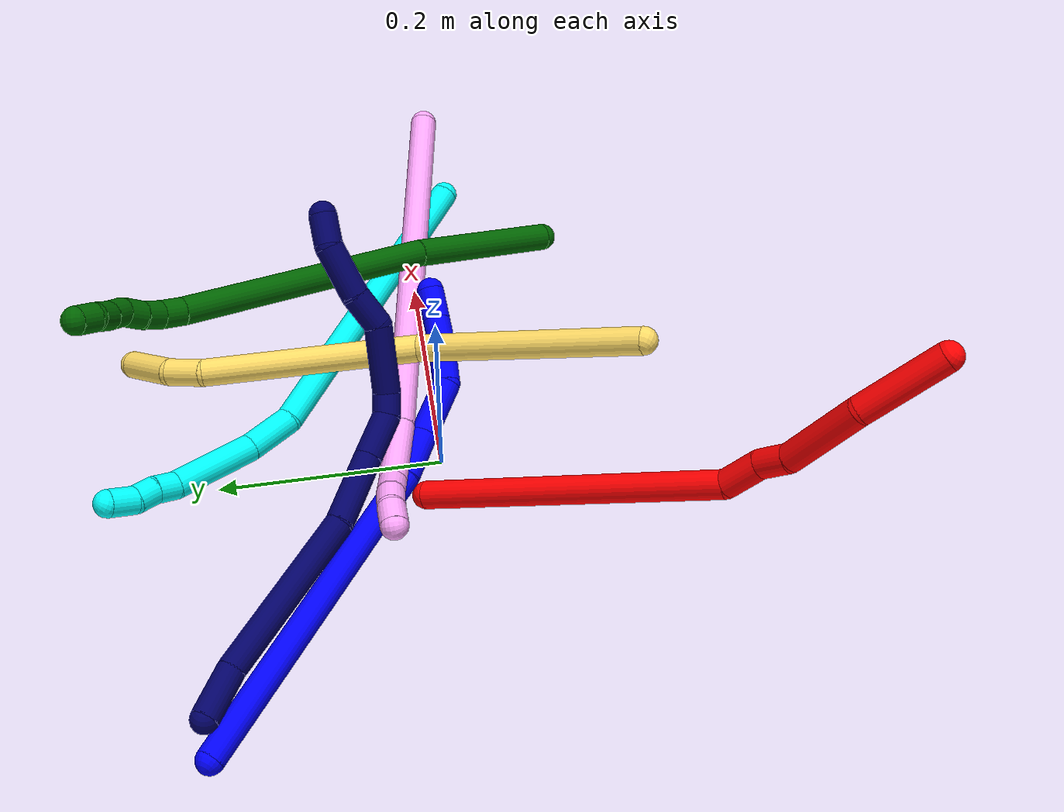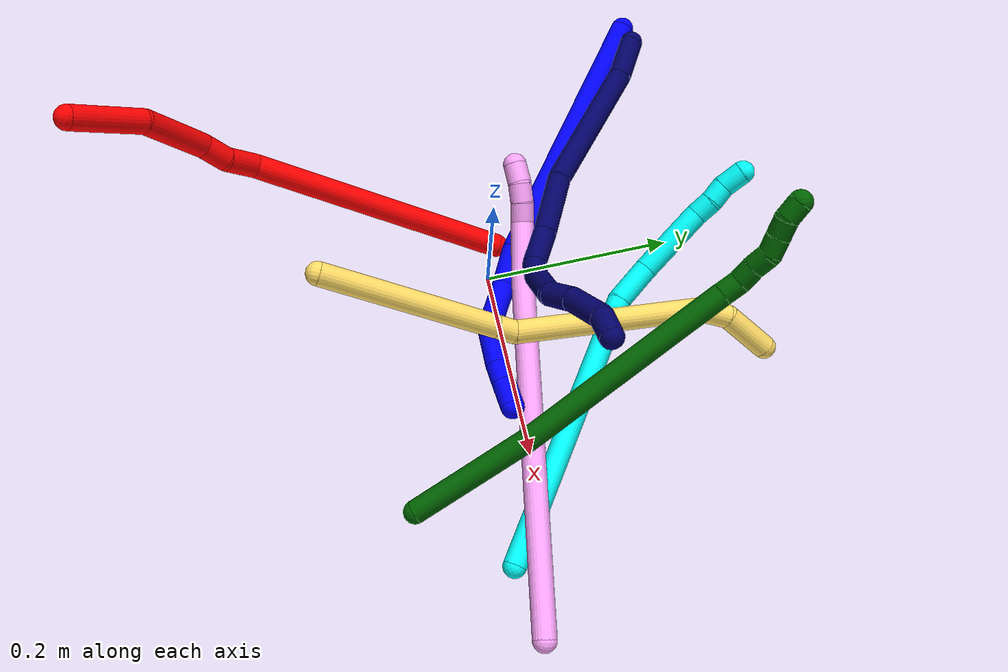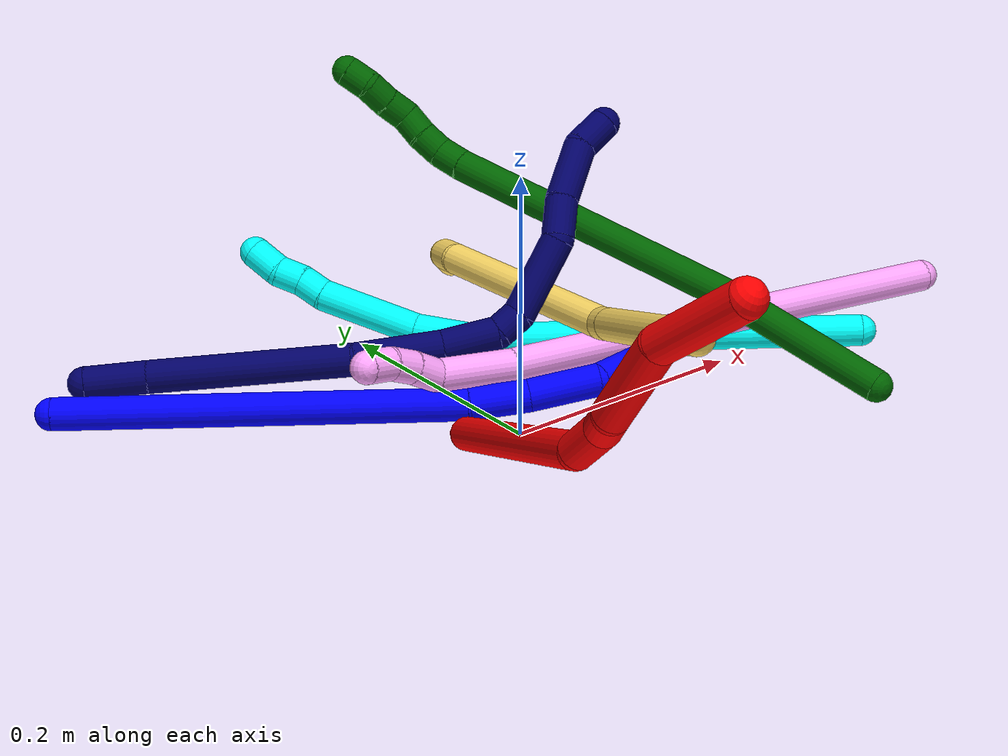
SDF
<sdf version="1.7">
 <world name="default">
  <plugin name="TubeGeneratorPlugin" filename="libtube_generator_plugin.so"/>
  <model name="photoneo_s_sensor">
   <static>1</static>
   <pose>0 0 2 1.57079 1.57079 3.14159</pose>
   <link name="link">
    <inertial><mass>0.1</mass></inertial>
    <sensor name="sensor" type="depth">
     <update_rate>30</update_rate>
     <camera>
      <horizontal_fov>1.22</horizontal_fov>
      <image><width>1920</width><height>1200</height><format>B8G8R8</format></image>
      <clip><near>0.1</near><far>4</far></clip>
      <depth_camera><output>points</output></depth_camera>
     </camera>
     <plugin name="camera_plugin" filename="libgazebo_ros_depth_camera.so">
      <baseline>0.2</baseline>
      <alwaysOn>1</alwaysOn>
      <updateRate>0.0</updateRate>
      <cameraName>camera_ir</cameraName>
      <imageTopicName>/camera/color/image_raw</imageTopicName>
      <cameraInfoTopicName>/camera/color/camera_info</cameraInfoTopicName>
      <depthImageTopicName>/camera/depth/image_raw</depthImageTopicName>
      <depthImageCameraInfoTopicName>/camera/depth/camera_info</depthImageCameraInfoTopicName>
      <pointCloudTopicName>/camera/depth/points</pointCloudTopicName>
      <frameName>fr_optical</frameName>
      <pointCloudCutoff>0.1</pointCloudCutoff>
      <pointCloudCutoffMax>2.0</pointCloudCutoffMax>
      <distortionK1>0</distortionK1>
      <distortionK2>0</distortionK2>
      <distortionK3>0</distortionK3>
      <distortionT1>0</distortionT1>
      <distortionT2>0</distortionT2>
      <CxPrime>0</CxPrime>
      <Cx>0</Cx>
      <Cy>0</Cy>
      <focalLength>0</focalLength>
      <hackBaseline>0</hackBaseline>
     </plugin>
    </sensor>
   </link>
  </model>
  <gravity>0 0 -9.8</gravity>
  <magnetic_field>6e-06 2.3e-05 -4.2e-05</magnetic_field>
  <atmosphere type="adiabatic"/>
  <physics name="default_physics" default="0" type="ode">
   <max_step_size>0.003</max_step_size>
   <real_time_factor>1</real_time_factor>
   <real_time_update_rate>1000</real_time_update_rate>
   <max_contacts>10000</max_contacts>
   <ode>
    <solver>
     <type>quick</type>
     <iters>100</iters>
     <sor>1.3</sor>
     <use_dynamic_moi_rescaling>0</use_dynamic_moi_rescaling>
    </solver>
    <constraints>
     <contact_max_correcting_vel>0</contact_max_correcting_vel>
     <contact_surface_layer>0.001</contact_surface_layer>
     <cfm>0</cfm>
     <erp>0.2</erp>
    </constraints>
   </ode>
  </physics>
  <scene><ambient>0.4 0.4 0.4 1</ambient><background>0.7 0.7 0.7 1</background><shadows>0</shadows></scene>
  <audio><device>default</device></audio>
  <spherical_coordinates>
   <surface_model>EARTH_WGS84</surface_model>
   <latitude_deg>0</latitude_deg>
   <longitude_deg>0</longitude_deg>
   <elevation>0</elevation>
   <heading_deg>0</heading_deg>
  </spherical_coordinates>
  <model name="bin">
   <static>1</static>
   <link name="bottom">
    <collision name="collision-bottom">
     <pose>0 0 -0.01 0 -0 0</pose>
     <geometry><box><size>0.8 0.6 0.02</size></box></geometry>
     <surface>
      <friction><ode><mu>100</mu><mu2>100</mu2></ode></friction>
      <contact><collide_bitmask>65535</collide_bitmask></contact>
     </surface>
    </collision>
   </link>
   <link name="west_wall">
    <collision name="collision-west_wall">
     <pose>-0.41 0 0.1 0 -0 0</pose>
     <geometry><box><size>0.02 0.6 0.2</size></box></geometry>
     <surface>
      <friction><ode><mu>100</mu><mu2>100</mu2></ode></friction>
      <contact><collide_bitmask>65535</collide_bitmask></contact>
     </surface>
    </collision>
   </link>
   <link name="east_wall">
    <collision name="collision-east_wall">
     <pose>0.41 0 0.1 0 -0 0</pose>
     <geometry><box><size>0.02 0.6 0.2</size></box></geometry>
     <surface>
      <friction><ode><mu>100</mu><mu2>100</mu2></ode></friction>
      <contact><collide_bitmask>65535</collide_bitmask></contact>
     </surface>
    </collision>
   </link>
   <link name="south_wall">
    <collision name="collision-south_wall">
     <pose>0 -0.31 0.1 0 -0 0</pose>
     <geometry><box><size>0.8 0.02 0.2</size></box></geometry>
     <surface>
      <friction><ode><mu>100</mu><mu2>100</mu2></ode></friction>
      <contact><collide_bitmask>65535</collide_bitmask></contact>
     </surface>
    </collision>
   </link>
   <link name="north_wall">
    <collision name="collision-north_wall">
     <pose>0 0.31 0.1 0 -0 0</pose>
     <geometry><box><size>0.8 0.02 0.2</size></box></geometry>
     <surface>
      <friction><ode><mu>100</mu><mu2>100</mu2></ode></friction>
      <contact><collide_bitmask>65535</collide_bitmask></contact>
     </surface>
    </collision>
   </link>
  </model>
  <model name="1">
   <static>0</static>
   <link name="1">
    <collision name="collision-cylinder-e_1_1_4">
     <pose>-0.007108 -0.011797 -0.151948 3.06411 -0.046606 -1.08274</pose>
     <geometry><cylinder><radius>0.0125</radius><length>0.305142</length></cylinder></geometry>
     <surface>
      <friction><ode><mu>1.16</mu><mu2>1.16</mu2><slip1>0</slip1><slip2>0</slip2></ode></friction>
      <contact><ode><kp>1e+06</kp><kd>1</kd><max_vel>0</max_vel><min_depth>0.001</min_depth></ode></contact>
     </surface>
    </collision>
    <visual name="visual-cylinder-e_1_1_4">
     <pose>-0.007108 -0.011797 -0.151948 3.06411 -0.046606 -1.08274</pose>
     <geometry><cylinder><radius>0.0125</radius><length>0.305142</length></cylinder></geometry>
     <material><ambient>0 0 1 1</ambient></material>
    </visual>
    <collision name="collision-cylinder-e_2_4_5">
     <pose>-0.011288 -0.024881 -0.326158 3.08386 0.130588 2.30991</pose>
     <geometry><cylinder><radius>0.0125</radius><length>0.044981</length></cylinder></geometry>
     <surface>
      <friction><ode><mu>1.16</mu><mu2>1.16</mu2><slip1>0</slip1><slip2>0</slip2></ode></friction>
      <contact><ode><kp>1e+06</kp><kd>1</kd><max_vel>0</max_vel><min_depth>0.001</min_depth></ode></contact>
     </surface>
    </collision>
    <visual name="visual-cylinder-e_2_4_5">
     <pose>-0.011288 -0.024881 -0.326158 3.08386 0.130588 2.30991</pose>
     <geometry><cylinder><radius>0.0125</radius><length>0.044981</length></cylinder></geometry>
     <material><ambient>0 0 1 1</ambient></material>
    </visual>
    <collision name="collision-cylinder-e_3_5_6">
     <pose>-0.004905 -0.030956 -0.374732 2.9616 0.12845 1.23838</pose>
     <geometry><cylinder><radius>0.0125</radius><length>0.053933</length></cylinder></geometry>
     <surface>
      <friction><ode><mu>1.16</mu><mu2>1.16</mu2><slip1>0</slip1><slip2>0</slip2></ode></friction>
      <contact><ode><kp>1e+06</kp><kd>1</kd><max_vel>0</max_vel><min_depth>0.001</min_depth></ode></contact>
     </surface>
    </collision>
    <visual name="visual-cylinder-e_3_5_6">
     <pose>-0.004905 -0.030956 -0.374732 2.9616 0.12845 1.23838</pose>
     <geometry><cylinder><radius>0.0125</radius><length>0.053933</length></cylinder></geometry>
     <material><ambient>0 0 1 1</ambient></material>
    </visual>
    <collision name="collision-cylinder-e_4_6_7">
     <pose>0.010289 -0.034239 -0.41915 -3.05865 0.573642 -2.86207</pose>
     <geometry><cylinder><radius>0.0125</radius><length>0.043262</length></cylinder></geometry>
     <surface>
      <friction><ode><mu>1.16</mu><mu2>1.16</mu2><slip1>0</slip1><slip2>0</slip2></ode></friction>
      <contact><ode><kp>1e+06</kp><kd>1</kd><max_vel>0</max_vel><min_depth>0.001</min_depth></ode></contact>
     </surface>
    </collision>
    <visual name="visual-cylinder-e_4_6_7">
     <pose>0.010289 -0.034239 -0.41915 -3.05865 0.573642 -2.86207</pose>
     <geometry><cylinder><radius>0.0125</radius><length>0.043262</length></cylinder></geometry>
     <material><ambient>0 0 1 1</ambient></material>
    </visual>
    <collision name="collision-cylinder-e_5_7_8">
     <pose>0.029648 -0.033719 -0.445978 3.02912 0.714929 2.8424</pose>
     <geometry><cylinder><radius>0.0125</radius><length>0.023247</length></cylinder></geometry>
     <surface>
      <friction><ode><mu>1.16</mu><mu2>1.16</mu2><slip1>0</slip1><slip2>0</slip2></ode></friction>
      <contact><ode><kp>1e+06</kp><kd>1</kd><max_vel>0</max_vel><min_depth>0.001</min_depth></ode></contact>
     </surface>
    </collision>
    <visual name="visual-cylinder-e_5_7_8">
     <pose>0.029648 -0.033719 -0.445978 3.02912 0.714929 2.8424</pose>
     <geometry><cylinder><radius>0.0125</radius><length>0.023247</length></cylinder></geometry>
     <material><ambient>0 0 1 1</ambient></material>
    </visual>
    <collision name="collision-cylinder-e_6_8_2">
     <pose>0.046965 -0.035866 -0.46571 3.0364 0.719322 2.8634</pose>
     <geometry><cylinder><radius>0.0125</radius><length>0.029435</length></cylinder></geometry>
     <surface>
      <friction><ode><mu>1.16</mu><mu2>1.16</mu2><slip1>0</slip1><slip2>0</slip2></ode></friction>
      <contact><ode><kp>1e+06</kp><kd>1</kd><max_vel>0</max_vel><min_depth>0.001</min_depth></ode></contact>
     </surface>
    </collision>
    <visual name="visual-cylinder-e_6_8_2">
     <pose>0.046965 -0.035866 -0.46571 3.0364 0.719322 2.8634</pose>
     <geometry><cylinder><radius>0.0125</radius><length>0.029435</length></cylinder></geometry>
     <material><ambient>0 0 1 1</ambient></material>
    </visual>
    <collision name="collision-sphere-2">
     <pose>0.056662 -0.037029 -0.47672 0 -0 0</pose>
     <geometry><sphere><radius>0.0125</radius></sphere></geometry>
     <surface>
      <friction><ode><mu>1.16</mu><mu2>1.16</mu2><slip1>0</slip1><slip2>0</slip2></ode></friction>
      <contact><ode><kp>1e+06</kp><kd>1</kd><max_vel>0</max_vel><min_depth>0.001</min_depth></ode></contact>
     </surface>
    </collision>
    <visual name="visual-sphere-2">
     <pose>0.056662 -0.037029 -0.47672 0 -0 0</pose>
     <geometry><sphere><radius>0.0125</radius></sphere></geometry>
     <material><ambient>0 0 1 1</ambient></material>
    </visual>
    <collision name="collision-sphere-4">
     <pose>-0.014216 -0.023595 -0.303896 0 -0 0</pose>
     <geometry><sphere><radius>0.0125</radius></sphere></geometry>
     <surface>
      <friction><ode><mu>1.16</mu><mu2>1.16</mu2><slip1>0</slip1><slip2>0</slip2></ode></friction>
      <contact><ode><kp>1e+06</kp><kd>1</kd><max_vel>0</max_vel><min_depth>0.001</min_depth></ode></contact>
     </surface>
    </collision>
    <visual name="visual-sphere-4">
     <pose>-0.014216 -0.023595 -0.303896 0 -0 0</pose>
     <geometry><sphere><radius>0.0125</radius></sphere></geometry>
     <material><ambient>0 0 1 1</ambient></material>
    </visual>
    <collision name="collision-sphere-1">
     <geometry><sphere><radius>0.0125</radius></sphere></geometry>
     <surface>
      <friction><ode><mu>1.16</mu><mu2>1.16</mu2><slip1>0</slip1><slip2>0</slip2></ode></friction>
      <contact><ode><kp>1e+06</kp><kd>1</kd><max_vel>0</max_vel><min_depth>0.001</min_depth></ode></contact>
     </surface>
    </collision>
    <visual name="visual-sphere-1">
     <geometry><sphere><radius>0.0125</radius></sphere></geometry>
     <material><ambient>0 0 1 1</ambient></material>
    </visual>
    <collision name="collision-sphere-8">
     <pose>0.037268 -0.034704 -0.4547 0 -0 0</pose>
     <geometry><sphere><radius>0.0125</radius></sphere></geometry>
     <surface>
      <friction><ode><mu>1.16</mu><mu2>1.16</mu2><slip1>0</slip1><slip2>0</slip2></ode></friction>
      <contact><ode><kp>1e+06</kp><kd>1</kd><max_vel>0</max_vel><min_depth>0.001</min_depth></ode></contact>
     </surface>
    </collision>
    <visual name="visual-sphere-8">
     <pose>0.037268 -0.034704 -0.4547 0 -0 0</pose>
     <geometry><sphere><radius>0.0125</radius></sphere></geometry>
     <material><ambient>0 0 1 1</ambient></material>
    </visual>
    <collision name="collision-sphere-5">
     <pose>-0.008359 -0.026168 -0.34842 0 -0 0</pose>
     <geometry><sphere><radius>0.0125</radius></sphere></geometry>
     <surface>
      <friction><ode><mu>1.16</mu><mu2>1.16</mu2><slip1>0</slip1><slip2>0</slip2></ode></friction>
      <contact><ode><kp>1e+06</kp><kd>1</kd><max_vel>0</max_vel><min_depth>0.001</min_depth></ode></contact>
     </surface>
    </collision>
    <visual name="visual-sphere-5">
     <pose>-0.008359 -0.026168 -0.34842 0 -0 0</pose>
     <geometry><sphere><radius>0.0125</radius></sphere></geometry>
     <material><ambient>0 0 1 1</ambient></material>
    </visual>
    <collision name="collision-sphere-6">
     <pose>-0.00145 -0.035744 -0.401044 0 -0 0</pose>
     <geometry><sphere><radius>0.0125</radius></sphere></geometry>
     <surface>
      <friction><ode><mu>1.16</mu><mu2>1.16</mu2><slip1>0</slip1><slip2>0</slip2></ode></friction>
      <contact><ode><kp>1e+06</kp><kd>1</kd><max_vel>0</max_vel><min_depth>0.001</min_depth></ode></contact>
     </surface>
    </collision>
    <visual name="visual-sphere-6">
     <pose>-0.00145 -0.035744 -0.401044 0 -0 0</pose>
     <geometry><sphere><radius>0.0125</radius></sphere></geometry>
     <material><ambient>0 0 1 1</ambient></material>
    </visual>
    <collision name="collision-sphere-7">
     <pose>0.022028 -0.032733 -0.437256 0 -0 0</pose>
     <geometry><sphere><radius>0.0125</radius></sphere></geometry>
     <surface>
      <friction><ode><mu>1.16</mu><mu2>1.16</mu2><slip1>0</slip1><slip2>0</slip2></ode></friction>
      <contact><ode><kp>1e+06</kp><kd>1</kd><max_vel>0</max_vel><min_depth>0.001</min_depth></ode></contact>
     </surface>
    </collision>
    <visual name="visual-sphere-7">
     <pose>0.022028 -0.032733 -0.437256 0 -0 0</pose>
     <geometry><sphere><radius>0.0125</radius></sphere></geometry>
     <material><ambient>0 0 1 1</ambient></material>
    </visual>
    <inertial>
     <pose>-0.000849 -0.019419 -0.246912 0 -0 0</pose>
     <mass>0.5</mass>
     <inertia>
      <ixx>-0.000972</ixx>
      <ixy>0</ixy>
      <ixz>0</ixz>
      <iyy>-0.003172</iyy>
      <iyz>0</iyz>
      <izz>0.00025</izz>
     </inertia>
    </inertial>
   </link>
   <pose>-0.262812 0.220316 0.011496 -1.53373 -0.384462 0.971792</pose>
  </model>
  <model name="2">
   <static>0</static>
   <link name="2">
    <collision name="collision-cylinder-e_1_1_4">
     <pose>-0.024727 -0.082832 0.10978 0.646395 -0.1779 -0.059726</pose>
     <geometry><cylinder><radius>0.0125</radius><length>0.279459</length></cylinder></geometry>
     <surface>
      <friction><ode><mu>1.16</mu><mu2>1.16</mu2><slip1>0</slip1><slip2>0</slip2></ode></friction>
      <contact><ode><kp>1e+06</kp><kd>1</kd><max_vel>0</max_vel><min_depth>0.001</min_depth></ode></contact>
     </surface>
    </collision>
    <visual name="visual-cylinder-e_1_1_4">
     <pose>-0.024727 -0.082832 0.10978 0.646395 -0.1779 -0.059726</pose>
     <geometry><cylinder><radius>0.0125</radius><length>0.279459</length></cylinder></geometry>
     <material><ambient>1 0 0 1</ambient></material>
    </visual>
    <collision name="collision-cylinder-e_2_4_5">
     <pose>-0.049421 -0.169401 0.23727 0.207919 0.001803 0.000188</pose>
     <geometry><cylinder><radius>0.0125</radius><length>0.036201</length></cylinder></geometry>
     <surface>
      <friction><ode><mu>1.16</mu><mu2>1.16</mu2><slip1>0</slip1><slip2>0</slip2></ode></friction>
      <contact><ode><kp>1e+06</kp><kd>1</kd><max_vel>0</max_vel><min_depth>0.001</min_depth></ode></contact>
     </surface>
    </collision>
    <visual name="visual-cylinder-e_2_4_5">
     <pose>-0.049421 -0.169401 0.23727 0.207919 0.001803 0.000188</pose>
     <geometry><cylinder><radius>0.0125</radius><length>0.036201</length></cylinder></geometry>
     <material><ambient>1 0 0 1</ambient></material>
    </visual>
    <collision name="collision-cylinder-e_3_5_6">
     <pose>-0.053813 -0.17755 0.267924 0.328542 -0.312954 -0.052292</pose>
     <geometry><cylinder><radius>0.0125</radius><length>0.028745</length></cylinder></geometry>
     <surface>
      <friction><ode><mu>1.16</mu><mu2>1.16</mu2><slip1>0</slip1><slip2>0</slip2></ode></friction>
      <contact><ode><kp>1e+06</kp><kd>1</kd><max_vel>0</max_vel><min_depth>0.001</min_depth></ode></contact>
     </surface>
    </collision>
    <visual name="visual-cylinder-e_3_5_6">
     <pose>-0.053813 -0.17755 0.267924 0.328542 -0.312954 -0.052292</pose>
     <geometry><cylinder><radius>0.0125</radius><length>0.028745</length></cylinder></geometry>
     <material><ambient>1 0 0 1</ambient></material>
    </visual>
    <collision name="collision-cylinder-e_4_6_7">
     <pose>-0.062084 -0.184664 0.319156 0.070458 -0.099862 -0.003522</pose>
     <geometry><cylinder><radius>0.0125</radius><length>0.077154</length></cylinder></geometry>
     <surface>
      <friction><ode><mu>1.16</mu><mu2>1.16</mu2><slip1>0</slip1><slip2>0</slip2></ode></friction>
      <contact><ode><kp>1e+06</kp><kd>1</kd><max_vel>0</max_vel><min_depth>0.001</min_depth></ode></contact>
     </surface>
    </collision>
    <visual name="visual-cylinder-e_4_6_7">
     <pose>-0.062084 -0.184664 0.319156 0.070458 -0.099862 -0.003522</pose>
     <geometry><cylinder><radius>0.0125</radius><length>0.077154</length></cylinder></geometry>
     <material><ambient>1 0 0 1</ambient></material>
    </visual>
    <collision name="collision-cylinder-e_5_7_2">
     <pose>-0.059961 -0.198214 0.394661 0.283631 0.152792 0.021856</pose>
     <geometry><cylinder><radius>0.0125</radius><length>0.078442</length></cylinder></geometry>
     <surface>
      <friction><ode><mu>1.16</mu><mu2>1.16</mu2><slip1>0</slip1><slip2>0</slip2></ode></friction>
      <contact><ode><kp>1e+06</kp><kd>1</kd><max_vel>0</max_vel><min_depth>0.001</min_depth></ode></contact>
     </surface>
    </collision>
    <visual name="visual-cylinder-e_5_7_2">
     <pose>-0.059961 -0.198214 0.394661 0.283631 0.152792 0.021856</pose>
     <geometry><cylinder><radius>0.0125</radius><length>0.078442</length></cylinder></geometry>
     <material><ambient>1 0 0 1</ambient></material>
    </visual>
    <collision name="collision-sphere-2">
     <pose>-0.053991 -0.209062 0.431876 0 -0 0</pose>
     <geometry><sphere><radius>0.0125</radius></sphere></geometry>
     <surface>
      <friction><ode><mu>1.16</mu><mu2>1.16</mu2><slip1>0</slip1><slip2>0</slip2></ode></friction>
      <contact><ode><kp>1e+06</kp><kd>1</kd><max_vel>0</max_vel><min_depth>0.001</min_depth></ode></contact>
     </surface>
    </collision>
    <visual name="visual-sphere-2">
     <pose>-0.053991 -0.209062 0.431876 0 -0 0</pose>
     <geometry><sphere><radius>0.0125</radius></sphere></geometry>
     <material><ambient>1 0 0 1</ambient></material>
    </visual>
    <collision name="collision-sphere-7">
     <pose>-0.06593 -0.187366 0.357446 0 -0 0</pose>
     <geometry><sphere><radius>0.0125</radius></sphere></geometry>
     <surface>
      <friction><ode><mu>1.16</mu><mu2>1.16</mu2><slip1>0</slip1><slip2>0</slip2></ode></friction>
      <contact><ode><kp>1e+06</kp><kd>1</kd><max_vel>0</max_vel><min_depth>0.001</min_depth></ode></contact>
     </surface>
    </collision>
    <visual name="visual-sphere-7">
     <pose>-0.06593 -0.187366 0.357446 0 -0 0</pose>
     <geometry><sphere><radius>0.0125</radius></sphere></geometry>
     <material><ambient>1 0 0 1</ambient></material>
    </visual>
    <collision name="collision-sphere-6">
     <pose>-0.058238 -0.181962 0.280867 0 -0 0</pose>
     <geometry><sphere><radius>0.0125</radius></sphere></geometry>
     <surface>
      <friction><ode><mu>1.16</mu><mu2>1.16</mu2><slip1>0</slip1><slip2>0</slip2></ode></friction>
      <contact><ode><kp>1e+06</kp><kd>1</kd><max_vel>0</max_vel><min_depth>0.001</min_depth></ode></contact>
     </surface>
    </collision>
    <visual name="visual-sphere-6">
     <pose>-0.058238 -0.181962 0.280867 0 -0 0</pose>
     <geometry><sphere><radius>0.0125</radius></sphere></geometry>
     <material><ambient>1 0 0 1</ambient></material>
    </visual>
    <collision name="collision-sphere-5">
     <pose>-0.049388 -0.173137 0.254981 0 -0 0</pose>
     <geometry><sphere><radius>0.0125</radius></sphere></geometry>
     <surface>
      <friction><ode><mu>1.16</mu><mu2>1.16</mu2><slip1>0</slip1><slip2>0</slip2></ode></friction>
      <contact><ode><kp>1e+06</kp><kd>1</kd><max_vel>0</max_vel><min_depth>0.001</min_depth></ode></contact>
     </surface>
    </collision>
    <visual name="visual-sphere-5">
     <pose>-0.049388 -0.173137 0.254981 0 -0 0</pose>
     <geometry><sphere><radius>0.0125</radius></sphere></geometry>
     <material><ambient>1 0 0 1</ambient></material>
    </visual>
    <collision name="collision-sphere-1">
     <geometry><sphere><radius>0.0125</radius></sphere></geometry>
     <surface>
      <friction><ode><mu>1.16</mu><mu2>1.16</mu2><slip1>0</slip1><slip2>0</slip2></ode></friction>
      <contact><ode><kp>1e+06</kp><kd>1</kd><max_vel>0</max_vel><min_depth>0.001</min_depth></ode></contact>
     </surface>
    </collision>
    <visual name="visual-sphere-1">
     <geometry><sphere><radius>0.0125</radius></sphere></geometry>
     <material><ambient>1 0 0 1</ambient></material>
    </visual>
    <collision name="collision-sphere-4">
     <pose>-0.049454 -0.165665 0.21956 0 -0 0</pose>
     <geometry><sphere><radius>0.0125</radius></sphere></geometry>
     <surface>
      <friction><ode><mu>1.16</mu><mu2>1.16</mu2><slip1>0</slip1><slip2>0</slip2></ode></friction>
      <contact><ode><kp>1e+06</kp><kd>1</kd><max_vel>0</max_vel><min_depth>0.001</min_depth></ode></contact>
     </surface>
    </collision>
    <visual name="visual-sphere-4">
     <pose>-0.049454 -0.165665 0.21956 0 -0 0</pose>
     <geometry><sphere><radius>0.0125</radius></sphere></geometry>
     <material><ambient>1 0 0 1</ambient></material>
    </visual>
    <inertial>
     <pose>-0.039479 -0.12836 0.205104 0 -0 0</pose>
     <mass>0.5</mass>
     <inertia>
      <ixx>0.001779</ixx>
      <ixy>0</ixy>
      <ixz>0</ixz>
      <iyy>0.001437</iyy>
      <iyz>0</iyz>
      <izz>0.001458</izz>
     </inertia>
    </inertial>
   </link>
   <pose>-0.034921 0.01782 0.004035 0.538499 0.259643 -0.305573</pose>
  </model>
  <model name="3">
   <static>0</static>
   <link name="3">
    <collision name="collision-cylinder-e_1_1_4">
     <pose>-0.116083 0.077307 0.063364 -0.884189 -0.859907 0.427485</pose>
     <geometry><cylinder><radius>0.0125</radius><length>0.306377</length></cylinder></geometry>
     <surface>
      <friction><ode><mu>1.16</mu><mu2>1.16</mu2><slip1>0</slip1><slip2>0</slip2></ode></friction>
      <contact><ode><kp>1e+06</kp><kd>1</kd><max_vel>0</max_vel><min_depth>0.001</min_depth></ode></contact>
     </surface>
    </collision>
    <visual name="visual-cylinder-e_1_1_4">
     <pose>-0.116083 0.077307 0.063364 -0.884189 -0.859907 0.427485</pose>
     <geometry><cylinder><radius>0.0125</radius><length>0.306377</length></cylinder></geometry>
     <material><ambient>0.003922 1 0.996078 1</ambient></material>
    </visual>
    <collision name="collision-cylinder-e_2_4_5">
     <pose>-0.244435 0.167256 0.141557 -0.70602 -0.561861 0.211842</pose>
     <geometry><cylinder><radius>0.0125</radius><length>0.046054</length></cylinder></geometry>
     <surface>
      <friction><ode><mu>1.16</mu><mu2>1.16</mu2><slip1>0</slip1><slip2>0</slip2></ode></friction>
      <contact><ode><kp>1e+06</kp><kd>1</kd><max_vel>0</max_vel><min_depth>0.001</min_depth></ode></contact>
     </surface>
    </collision>
    <visual name="visual-cylinder-e_2_4_5">
     <pose>-0.244435 0.167256 0.141557 -0.70602 -0.561861 0.211842</pose>
     <geometry><cylinder><radius>0.0125</radius><length>0.046054</length></cylinder></geometry>
     <material><ambient>0.003922 1 0.996078 1</ambient></material>
    </visual>
    <collision name="collision-cylinder-e_3_5_6">
     <pose>-0.276787 0.196698 0.186981 -0.502122 -0.522157 0.136833</pose>
     <geometry><cylinder><radius>0.0125</radius><length>0.08054</length></cylinder></geometry>
     <surface>
      <friction><ode><mu>1.16</mu><mu2>1.16</mu2><slip1>0</slip1><slip2>0</slip2></ode></friction>
      <contact><ode><kp>1e+06</kp><kd>1</kd><max_vel>0</max_vel><min_depth>0.001</min_depth></ode></contact>
     </surface>
    </collision>
    <visual name="visual-cylinder-e_3_5_6">
     <pose>-0.276787 0.196698 0.186981 -0.502122 -0.522157 0.136833</pose>
     <geometry><cylinder><radius>0.0125</radius><length>0.08054</length></cylinder></geometry>
     <material><ambient>0.003922 1 0.996078 1</ambient></material>
    </visual>
    <collision name="collision-cylinder-e_4_6_7">
     <pose>-0.300838 0.216154 0.226873 -0.278399 -0.389252 0.055222</pose>
     <geometry><cylinder><radius>0.0125</radius><length>0.020902</length></cylinder></geometry>
     <surface>
      <friction><ode><mu>1.16</mu><mu2>1.16</mu2><slip1>0</slip1><slip2>0</slip2></ode></friction>
      <contact><ode><kp>1e+06</kp><kd>1</kd><max_vel>0</max_vel><min_depth>0.001</min_depth></ode></contact>
     </surface>
    </collision>
    <visual name="visual-cylinder-e_4_6_7">
     <pose>-0.300838 0.216154 0.226873 -0.278399 -0.389252 0.055222</pose>
     <geometry><cylinder><radius>0.0125</radius><length>0.020902</length></cylinder></geometry>
     <material><ambient>0.003922 1 0.996078 1</ambient></material>
    </visual>
    <collision name="collision-cylinder-e_5_7_8">
     <pose>-0.310623 0.222325 0.243993 -0.422058 -0.596197 0.131449</pose>
     <geometry><cylinder><radius>0.0125</radius><length>0.020727</length></cylinder></geometry>
     <surface>
      <friction><ode><mu>1.16</mu><mu2>1.16</mu2><slip1>0</slip1><slip2>0</slip2></ode></friction>
      <contact><ode><kp>1e+06</kp><kd>1</kd><max_vel>0</max_vel><min_depth>0.001</min_depth></ode></contact>
     </surface>
    </collision>
    <visual name="visual-cylinder-e_5_7_8">
     <pose>-0.310623 0.222325 0.243993 -0.422058 -0.596197 0.131449</pose>
     <geometry><cylinder><radius>0.0125</radius><length>0.020727</length></cylinder></geometry>
     <material><ambient>0.003922 1 0.996078 1</ambient></material>
    </visual>
    <collision name="collision-cylinder-e_6_8_2">
     <pose>-0.320258 0.228723 0.263581 -0.240529 -0.305163 0.037163</pose>
     <geometry><cylinder><radius>0.0125</radius><length>0.0254</length></cylinder></geometry>
     <surface>
      <friction><ode><mu>1.16</mu><mu2>1.16</mu2><slip1>0</slip1><slip2>0</slip2></ode></friction>
      <contact><ode><kp>1e+06</kp><kd>1</kd><max_vel>0</max_vel><min_depth>0.001</min_depth></ode></contact>
     </surface>
    </collision>
    <visual name="visual-cylinder-e_6_8_2">
     <pose>-0.320258 0.228723 0.263581 -0.240529 -0.305163 0.037163</pose>
     <geometry><cylinder><radius>0.0125</radius><length>0.0254</length></cylinder></geometry>
     <material><ambient>0.003922 1 0.996078 1</ambient></material>
    </visual>
    <collision name="collision-sphere-2">
     <pose>-0.324074 0.231609 0.275345 0 -0 0</pose>
     <geometry><sphere><radius>0.0125</radius></sphere></geometry>
     <surface>
      <friction><ode><mu>1.16</mu><mu2>1.16</mu2><slip1>0</slip1><slip2>0</slip2></ode></friction>
      <contact><ode><kp>1e+06</kp><kd>1</kd><max_vel>0</max_vel><min_depth>0.001</min_depth></ode></contact>
     </surface>
    </collision>
    <visual name="visual-sphere-2">
     <pose>-0.324074 0.231609 0.275345 0 -0 0</pose>
     <geometry><sphere><radius>0.0125</radius></sphere></geometry>
     <material><ambient>0.003922 1 0.996078 1</ambient></material>
    </visual>
    <collision name="collision-sphere-4">
     <pose>-0.232167 0.154613 0.126728 0 -0 0</pose>
     <geometry><sphere><radius>0.0125</radius></sphere></geometry>
     <surface>
      <friction><ode><mu>1.16</mu><mu2>1.16</mu2><slip1>0</slip1><slip2>0</slip2></ode></friction>
      <contact><ode><kp>1e+06</kp><kd>1</kd><max_vel>0</max_vel><min_depth>0.001</min_depth></ode></contact>
     </surface>
    </collision>
    <visual name="visual-sphere-4">
     <pose>-0.232167 0.154613 0.126728 0 -0 0</pose>
     <geometry><sphere><radius>0.0125</radius></sphere></geometry>
     <material><ambient>0.003922 1 0.996078 1</ambient></material>
    </visual>
    <collision name="collision-sphere-1">
     <geometry><sphere><radius>0.0125</radius></sphere></geometry>
     <surface>
      <friction><ode><mu>1.16</mu><mu2>1.16</mu2><slip1>0</slip1><slip2>0</slip2></ode></friction>
      <contact><ode><kp>1e+06</kp><kd>1</kd><max_vel>0</max_vel><min_depth>0.001</min_depth></ode></contact>
     </surface>
    </collision>
    <visual name="visual-sphere-1">
     <geometry><sphere><radius>0.0125</radius></sphere></geometry>
     <material><ambient>0.003922 1 0.996078 1</ambient></material>
    </visual>
    <collision name="collision-sphere-8">
     <pose>-0.316443 0.225838 0.251816 0 -0 0</pose>
     <geometry><sphere><radius>0.0125</radius></sphere></geometry>
     <surface>
      <friction><ode><mu>1.16</mu><mu2>1.16</mu2><slip1>0</slip1><slip2>0</slip2></ode></friction>
      <contact><ode><kp>1e+06</kp><kd>1</kd><max_vel>0</max_vel><min_depth>0.001</min_depth></ode></contact>
     </surface>
    </collision>
    <visual name="visual-sphere-8">
     <pose>-0.316443 0.225838 0.251816 0 -0 0</pose>
     <geometry><sphere><radius>0.0125</radius></sphere></geometry>
     <material><ambient>0.003922 1 0.996078 1</ambient></material>
    </visual>
    <collision name="collision-sphere-5">
     <pose>-0.256703 0.1799 0.156385 0 -0 0</pose>
     <geometry><sphere><radius>0.0125</radius></sphere></geometry>
     <surface>
      <friction><ode><mu>1.16</mu><mu2>1.16</mu2><slip1>0</slip1><slip2>0</slip2></ode></friction>
      <contact><ode><kp>1e+06</kp><kd>1</kd><max_vel>0</max_vel><min_depth>0.001</min_depth></ode></contact>
     </surface>
    </collision>
    <visual name="visual-sphere-5">
     <pose>-0.256703 0.1799 0.156385 0 -0 0</pose>
     <geometry><sphere><radius>0.0125</radius></sphere></geometry>
     <material><ambient>0.003922 1 0.996078 1</ambient></material>
    </visual>
    <collision name="collision-sphere-6">
     <pose>-0.296872 0.213497 0.217576 0 -0 0</pose>
     <geometry><sphere><radius>0.0125</radius></sphere></geometry>
     <surface>
      <friction><ode><mu>1.16</mu><mu2>1.16</mu2><slip1>0</slip1><slip2>0</slip2></ode></friction>
      <contact><ode><kp>1e+06</kp><kd>1</kd><max_vel>0</max_vel><min_depth>0.001</min_depth></ode></contact>
     </surface>
    </collision>
    <visual name="visual-sphere-6">
     <pose>-0.296872 0.213497 0.217576 0 -0 0</pose>
     <geometry><sphere><radius>0.0125</radius></sphere></geometry>
     <material><ambient>0.003922 1 0.996078 1</ambient></material>
    </visual>
    <collision name="collision-sphere-7">
     <pose>-0.304804 0.218812 0.23617 0 -0 0</pose>
     <geometry><sphere><radius>0.0125</radius></sphere></geometry>
     <surface>
      <friction><ode><mu>1.16</mu><mu2>1.16</mu2><slip1>0</slip1><slip2>0</slip2></ode></friction>
      <contact><ode><kp>1e+06</kp><kd>1</kd><max_vel>0</max_vel><min_depth>0.001</min_depth></ode></contact>
     </surface>
    </collision>
    <visual name="visual-sphere-7">
     <pose>-0.304804 0.218812 0.23617 0 -0 0</pose>
     <geometry><sphere><radius>0.0125</radius></sphere></geometry>
     <material><ambient>0.003922 1 0.996078 1</ambient></material>
    </visual>
    <inertial>
     <pose>-0.179952 0.124331 0.114973 0 -0 0</pose>
     <mass>0.5</mass>
     <inertia>
      <ixx>0.002117</ixx>
      <ixy>0</ixy>
      <ixz>0</ixz>
      <iyy>0.002707</iyy>
      <iyz>0</iyz>
      <izz>0.000636</izz>
     </inertia>
    </inertial>
   </link>
   <pose>0.309725 -0.043417 0.01146 -0.906077 0.189602 0.082566</pose>
  </model>
  <model name="4">
   <static>0</static>
   <link name="4">
    <collision name="collision-cylinder-e_1_1_4">
     <pose>-0.179604 -0.054889 -0.002141 1.60979 -1.27399 -1.31149</pose>
     <geometry><cylinder><radius>0.0125</radius><length>0.375632</length></cylinder></geometry>
     <surface>
      <friction><ode><mu>1.16</mu><mu2>1.16</mu2><slip1>0</slip1><slip2>0</slip2></ode></friction>
      <contact><ode><kp>1e+06</kp><kd>1</kd><max_vel>0</max_vel><min_depth>0.001</min_depth></ode></contact>
     </surface>
    </collision>
    <visual name="visual-cylinder-e_1_1_4">
     <pose>-0.179604 -0.054889 -0.002141 1.60979 -1.27399 -1.31149</pose>
     <geometry><cylinder><radius>0.0125</radius><length>0.375632</length></cylinder></geometry>
     <material><ambient>1 0.65098 0.996078 1</ambient></material>
    </visual>
    <collision name="collision-cylinder-e_2_4_5">
     <pose>-0.388872 -0.116798 -0.005576 1.75303 -1.33462 -1.51568</pose>
     <geometry><cylinder><radius>0.0125</radius><length>0.061021</length></cylinder></geometry>
     <surface>
      <friction><ode><mu>1.16</mu><mu2>1.16</mu2><slip1>0</slip1><slip2>0</slip2></ode></friction>
      <contact><ode><kp>1e+06</kp><kd>1</kd><max_vel>0</max_vel><min_depth>0.001</min_depth></ode></contact>
     </surface>
    </collision>
    <visual name="visual-cylinder-e_2_4_5">
     <pose>-0.388872 -0.116798 -0.005576 1.75303 -1.33462 -1.51568</pose>
     <geometry><cylinder><radius>0.0125</radius><length>0.061021</length></cylinder></geometry>
     <material><ambient>1 0.65098 0.996078 1</ambient></material>
    </visual>
    <collision name="collision-cylinder-e_3_5_6">
     <pose>-0.429195 -0.121751 -0.005413 -0.957095 -1.33783 0.778333</pose>
     <geometry><cylinder><radius>0.0125</radius><length>0.021912</length></cylinder></geometry>
     <surface>
      <friction><ode><mu>1.16</mu><mu2>1.16</mu2><slip1>0</slip1><slip2>0</slip2></ode></friction>
      <contact><ode><kp>1e+06</kp><kd>1</kd><max_vel>0</max_vel><min_depth>0.001</min_depth></ode></contact>
     </surface>
    </collision>
    <visual name="visual-cylinder-e_3_5_6">
     <pose>-0.429195 -0.121751 -0.005413 -0.957095 -1.33783 0.778333</pose>
     <geometry><cylinder><radius>0.0125</radius><length>0.021912</length></cylinder></geometry>
     <material><ambient>1 0.65098 0.996078 1</ambient></material>
    </visual>
    <collision name="collision-cylinder-e_4_6_7">
     <pose>-0.449725 -0.119154 -0.00201 -0.265377 -1.36915 0.21704</pose>
     <geometry><cylinder><radius>0.0125</radius><length>0.020147</length></cylinder></geometry>
     <surface>
      <friction><ode><mu>1.16</mu><mu2>1.16</mu2><slip1>0</slip1><slip2>0</slip2></ode></friction>
      <contact><ode><kp>1e+06</kp><kd>1</kd><max_vel>0</max_vel><min_depth>0.001</min_depth></ode></contact>
     </surface>
    </collision>
    <visual name="visual-cylinder-e_4_6_7">
     <pose>-0.449725 -0.119154 -0.00201 -0.265377 -1.36915 0.21704</pose>
     <geometry><cylinder><radius>0.0125</radius><length>0.020147</length></cylinder></geometry>
     <material><ambient>1 0.65098 0.996078 1</ambient></material>
    </visual>
    <collision name="collision-cylinder-e_5_7_2">
     <pose>-0.469746 -0.120818 0.002264 0.755893 -1.26568 -0.566753</pose>
     <geometry><cylinder><radius>0.0125</radius><length>0.021287</length></cylinder></geometry>
     <surface>
      <friction><ode><mu>1.16</mu><mu2>1.16</mu2><slip1>0</slip1><slip2>0</slip2></ode></friction>
      <contact><ode><kp>1e+06</kp><kd>1</kd><max_vel>0</max_vel><min_depth>0.001</min_depth></ode></contact>
     </surface>
    </collision>
    <visual name="visual-cylinder-e_5_7_2">
     <pose>-0.469746 -0.120818 0.002264 0.755893 -1.26568 -0.566753</pose>
     <geometry><cylinder><radius>0.0125</radius><length>0.021287</length></cylinder></geometry>
     <material><ambient>1 0.65098 0.996078 1</ambient></material>
    </visual>
    <collision name="collision-sphere-2">
     <pose>-0.479898 -0.123012 0.00459 0 -0 0</pose>
     <geometry><sphere><radius>0.0125</radius></sphere></geometry>
     <surface>
      <friction><ode><mu>1.16</mu><mu2>1.16</mu2><slip1>0</slip1><slip2>0</slip2></ode></friction>
      <contact><ode><kp>1e+06</kp><kd>1</kd><max_vel>0</max_vel><min_depth>0.001</min_depth></ode></contact>
     </surface>
    </collision>
    <visual name="visual-sphere-2">
     <pose>-0.479898 -0.123012 0.00459 0 -0 0</pose>
     <geometry><sphere><radius>0.0125</radius></sphere></geometry>
     <material><ambient>1 0.65098 0.996078 1</ambient></material>
    </visual>
    <collision name="collision-sphere-7">
     <pose>-0.459595 -0.118625 -6.3e-05 0 -0 0</pose>
     <geometry><sphere><radius>0.0125</radius></sphere></geometry>
     <surface>
      <friction><ode><mu>1.16</mu><mu2>1.16</mu2><slip1>0</slip1><slip2>0</slip2></ode></friction>
      <contact><ode><kp>1e+06</kp><kd>1</kd><max_vel>0</max_vel><min_depth>0.001</min_depth></ode></contact>
     </surface>
    </collision>
    <visual name="visual-sphere-7">
     <pose>-0.459595 -0.118625 -6.3e-05 0 -0 0</pose>
     <geometry><sphere><radius>0.0125</radius></sphere></geometry>
     <material><ambient>1 0.65098 0.996078 1</ambient></material>
    </visual>
    <collision name="collision-sphere-6">
     <pose>-0.439855 -0.119683 -0.003957 0 -0 0</pose>
     <geometry><sphere><radius>0.0125</radius></sphere></geometry>
     <surface>
      <friction><ode><mu>1.16</mu><mu2>1.16</mu2><slip1>0</slip1><slip2>0</slip2></ode></friction>
      <contact><ode><kp>1e+06</kp><kd>1</kd><max_vel>0</max_vel><min_depth>0.001</min_depth></ode></contact>
     </surface>
    </collision>
    <visual name="visual-sphere-6">
     <pose>-0.439855 -0.119683 -0.003957 0 -0 0</pose>
     <geometry><sphere><radius>0.0125</radius></sphere></geometry>
     <material><ambient>1 0.65098 0.996078 1</ambient></material>
    </visual>
    <collision name="collision-sphere-5">
     <pose>-0.418535 -0.123819 -0.00687 0 -0 0</pose>
     <geometry><sphere><radius>0.0125</radius></sphere></geometry>
     <surface>
      <friction><ode><mu>1.16</mu><mu2>1.16</mu2><slip1>0</slip1><slip2>0</slip2></ode></friction>
      <contact><ode><kp>1e+06</kp><kd>1</kd><max_vel>0</max_vel><min_depth>0.001</min_depth></ode></contact>
     </surface>
    </collision>
    <visual name="visual-sphere-5">
     <pose>-0.418535 -0.123819 -0.00687 0 -0 0</pose>
     <geometry><sphere><radius>0.0125</radius></sphere></geometry>
     <material><ambient>1 0.65098 0.996078 1</ambient></material>
    </visual>
    <collision name="collision-sphere-1">
     <geometry><sphere><radius>0.0125</radius></sphere></geometry>
     <surface>
      <friction><ode><mu>1.16</mu><mu2>1.16</mu2><slip1>0</slip1><slip2>0</slip2></ode></friction>
      <contact><ode><kp>1e+06</kp><kd>1</kd><max_vel>0</max_vel><min_depth>0.001</min_depth></ode></contact>
     </surface>
    </collision>
    <visual name="visual-sphere-1">
     <geometry><sphere><radius>0.0125</radius></sphere></geometry>
     <material><ambient>1 0.65098 0.996078 1</ambient></material>
    </visual>
    <collision name="collision-sphere-4">
     <pose>-0.359208 -0.109777 -0.004282 0 -0 0</pose>
     <geometry><sphere><radius>0.0125</radius></sphere></geometry>
     <surface>
      <friction><ode><mu>1.16</mu><mu2>1.16</mu2><slip1>0</slip1><slip2>0</slip2></ode></friction>
      <contact><ode><kp>1e+06</kp><kd>1</kd><max_vel>0</max_vel><min_depth>0.001</min_depth></ode></contact>
     </surface>
    </collision>
    <visual name="visual-sphere-4">
     <pose>-0.359208 -0.109777 -0.004282 0 -0 0</pose>
     <geometry><sphere><radius>0.0125</radius></sphere></geometry>
     <material><ambient>1 0.65098 0.996078 1</ambient></material>
    </visual>
    <inertial>
     <pose>-0.239319 -0.070771 -0.002511 0 -0 0</pose>
     <mass>0.5</mass>
     <inertia>
      <ixx>-0.000962</ixx>
      <ixy>0</ixy>
      <ixz>0</ixz>
      <iyy>0.002806</iyy>
      <iyz>0</iyz>
      <izz>0.005563</izz>
     </inertia>
    </inertial>
   </link>
   <pose>0.388501 -0.033378 0.034358 1.25732 0.296254 -0.256961</pose>
  </model>
  <model name="5">
   <static>0</static>
   <link name="5">
    <collision name="collision-cylinder-e_1_1_4">
     <pose>0.020339 0.094131 0.01041 -1.46066 0.211545 -0.18958</pose>
     <geometry><cylinder><radius>0.0125</radius><length>0.193729</length></cylinder></geometry>
     <surface>
      <friction><ode><mu>1.16</mu><mu2>1.16</mu2><slip1>0</slip1><slip2>0</slip2></ode></friction>
      <contact><ode><kp>1e+06</kp><kd>1</kd><max_vel>0</max_vel><min_depth>0.001</min_depth></ode></contact>
     </surface>
    </collision>
    <visual name="visual-cylinder-e_1_1_4">
     <pose>0.020339 0.094131 0.01041 -1.46066 0.211545 -0.18958</pose>
     <geometry><cylinder><radius>0.0125</radius><length>0.193729</length></cylinder></geometry>
     <material><ambient>1 0.858824 0.4 1</ambient></material>
    </visual>
    <collision name="collision-cylinder-e_2_4_5">
     <pose>0.042872 0.19841 0.02194 -1.46076 0.211733 -0.189768</pose>
     <geometry><cylinder><radius>0.0125</radius><length>0.020886</length></cylinder></geometry>
     <surface>
      <friction><ode><mu>1.16</mu><mu2>1.16</mu2><slip1>0</slip1><slip2>0</slip2></ode></friction>
      <contact><ode><kp>1e+06</kp><kd>1</kd><max_vel>0</max_vel><min_depth>0.001</min_depth></ode></contact>
     </surface>
    </collision>
    <visual name="visual-cylinder-e_2_4_5">
     <pose>0.042872 0.19841 0.02194 -1.46076 0.211733 -0.189768</pose>
     <geometry><cylinder><radius>0.0125</radius><length>0.020886</length></cylinder></geometry>
     <material><ambient>1 0.858824 0.4 1</ambient></material>
    </visual>
    <collision name="collision-cylinder-e_3_5_6">
     <pose>0.090558 0.285802 0.062231 -1.10149 0.483653 -0.300669</pose>
     <geometry><cylinder><radius>0.0125</radius><length>0.195656</length></cylinder></geometry>
     <surface>
      <friction><ode><mu>1.16</mu><mu2>1.16</mu2><slip1>0</slip1><slip2>0</slip2></ode></friction>
      <contact><ode><kp>1e+06</kp><kd>1</kd><max_vel>0</max_vel><min_depth>0.001</min_depth></ode></contact>
     </surface>
    </collision>
    <visual name="visual-cylinder-e_3_5_6">
     <pose>0.090558 0.285802 0.062231 -1.10149 0.483653 -0.300669</pose>
     <geometry><cylinder><radius>0.0125</radius><length>0.195656</length></cylinder></geometry>
     <material><ambient>1 0.858824 0.4 1</ambient></material>
    </visual>
    <collision name="collision-cylinder-e_4_6_7">
     <pose>0.141317 0.379135 0.103528 -1.43941 0.313821 -0.2756</pose>
     <geometry><cylinder><radius>0.0125</radius><length>0.034126</length></cylinder></geometry>
     <surface>
      <friction><ode><mu>1.16</mu><mu2>1.16</mu2><slip1>0</slip1><slip2>0</slip2></ode></friction>
      <contact><ode><kp>1e+06</kp><kd>1</kd><max_vel>0</max_vel><min_depth>0.001</min_depth></ode></contact>
     </surface>
    </collision>
    <visual name="visual-cylinder-e_4_6_7">
     <pose>0.141317 0.379135 0.103528 -1.43941 0.313821 -0.2756</pose>
     <geometry><cylinder><radius>0.0125</radius><length>0.034126</length></cylinder></geometry>
     <material><ambient>1 0.858824 0.4 1</ambient></material>
    </visual>
    <collision name="collision-cylinder-e_5_7_2">
     <pose>0.147438 0.422496 0.100317 -1.76406 0.030724 -0.037318</pose>
     <geometry><cylinder><radius>0.0125</radius><length>0.055603</length></cylinder></geometry>
     <surface>
      <friction><ode><mu>1.16</mu><mu2>1.16</mu2><slip1>0</slip1><slip2>0</slip2></ode></friction>
      <contact><ode><kp>1e+06</kp><kd>1</kd><max_vel>0</max_vel><min_depth>0.001</min_depth></ode></contact>
     </surface>
    </collision>
    <visual name="visual-cylinder-e_5_7_2">
     <pose>0.147438 0.422496 0.100317 -1.76406 0.030724 -0.037318</pose>
     <geometry><cylinder><radius>0.0125</radius><length>0.055603</length></cylinder></geometry>
     <material><ambient>1 0.858824 0.4 1</ambient></material>
    </visual>
    <collision name="collision-sphere-2">
     <pose>0.148292 0.449767 0.09498 0 -0 0</pose>
     <geometry><sphere><radius>0.0125</radius></sphere></geometry>
     <surface>
      <friction><ode><mu>1.16</mu><mu2>1.16</mu2><slip1>0</slip1><slip2>0</slip2></ode></friction>
      <contact><ode><kp>1e+06</kp><kd>1</kd><max_vel>0</max_vel><min_depth>0.001</min_depth></ode></contact>
     </surface>
    </collision>
    <visual name="visual-sphere-2">
     <pose>0.148292 0.449767 0.09498 0 -0 0</pose>
     <geometry><sphere><radius>0.0125</radius></sphere></geometry>
     <material><ambient>1 0.858824 0.4 1</ambient></material>
    </visual>
    <collision name="collision-sphere-7">
     <pose>0.146584 0.395225 0.105654 0 -0 0</pose>
     <geometry><sphere><radius>0.0125</radius></sphere></geometry>
     <surface>
      <friction><ode><mu>1.16</mu><mu2>1.16</mu2><slip1>0</slip1><slip2>0</slip2></ode></friction>
      <contact><ode><kp>1e+06</kp><kd>1</kd><max_vel>0</max_vel><min_depth>0.001</min_depth></ode></contact>
     </surface>
    </collision>
    <visual name="visual-sphere-7">
     <pose>0.146584 0.395225 0.105654 0 -0 0</pose>
     <geometry><sphere><radius>0.0125</radius></sphere></geometry>
     <material><ambient>1 0.858824 0.4 1</ambient></material>
    </visual>
    <collision name="collision-sphere-6">
     <pose>0.13605 0.363045 0.101401 0 -0 0</pose>
     <geometry><sphere><radius>0.0125</radius></sphere></geometry>
     <surface>
      <friction><ode><mu>1.16</mu><mu2>1.16</mu2><slip1>0</slip1><slip2>0</slip2></ode></friction>
      <contact><ode><kp>1e+06</kp><kd>1</kd><max_vel>0</max_vel><min_depth>0.001</min_depth></ode></contact>
     </surface>
    </collision>
    <visual name="visual-sphere-6">
     <pose>0.13605 0.363045 0.101401 0 -0 0</pose>
     <geometry><sphere><radius>0.0125</radius></sphere></geometry>
     <material><ambient>1 0.858824 0.4 1</ambient></material>
    </visual>
    <collision name="collision-sphere-5">
     <pose>0.045067 0.208558 0.023062 0 -0 0</pose>
     <geometry><sphere><radius>0.0125</radius></sphere></geometry>
     <surface>
      <friction><ode><mu>1.16</mu><mu2>1.16</mu2><slip1>0</slip1><slip2>0</slip2></ode></friction>
      <contact><ode><kp>1e+06</kp><kd>1</kd><max_vel>0</max_vel><min_depth>0.001</min_depth></ode></contact>
     </surface>
    </collision>
    <visual name="visual-sphere-5">
     <pose>0.045067 0.208558 0.023062 0 -0 0</pose>
     <geometry><sphere><radius>0.0125</radius></sphere></geometry>
     <material><ambient>1 0.858824 0.4 1</ambient></material>
    </visual>
    <collision name="collision-sphere-1">
     <geometry><sphere><radius>0.0125</radius></sphere></geometry>
     <surface>
      <friction><ode><mu>1.16</mu><mu2>1.16</mu2><slip1>0</slip1><slip2>0</slip2></ode></friction>
      <contact><ode><kp>1e+06</kp><kd>1</kd><max_vel>0</max_vel><min_depth>0.001</min_depth></ode></contact>
     </surface>
    </collision>
    <visual name="visual-sphere-1">
     <geometry><sphere><radius>0.0125</radius></sphere></geometry>
     <material><ambient>1 0.858824 0.4 1</ambient></material>
    </visual>
    <collision name="collision-sphere-4">
     <pose>0.040677 0.188262 0.020819 0 -0 0</pose>
     <geometry><sphere><radius>0.0125</radius></sphere></geometry>
     <surface>
      <friction><ode><mu>1.16</mu><mu2>1.16</mu2><slip1>0</slip1><slip2>0</slip2></ode></friction>
      <contact><ode><kp>1e+06</kp><kd>1</kd><max_vel>0</max_vel><min_depth>0.001</min_depth></ode></contact>
     </surface>
    </collision>
    <visual name="visual-sphere-4">
     <pose>0.040677 0.188262 0.020819 0 -0 0</pose>
     <geometry><sphere><radius>0.0125</radius></sphere></geometry>
     <material><ambient>1 0.858824 0.4 1</ambient></material>
    </visual>
    <inertial>
     <pose>0.071149 0.229459 0.047524 0 -0 0</pose>
     <mass>0.5</mass>
     <inertia>
      <ixx>0.000876</ixx>
      <ixy>0</ixy>
      <ixz>0</ixz>
      <iyy>0.000193</iyy>
      <iyz>0</iyz>
      <izz>-0.001535</izz>
     </inertia>
    </inertial>
   </link>
   <pose>0.00617 -0.177146 0.138746 -1.78032 -0.993352 1.27714</pose>
  </model>
  <model name="6">
   <static>0</static>
   <link name="6">
    <collision name="collision-cylinder-e_1_1_4">
     <pose>-0.033585 0.020347 0.055869 -0.349262 -0.514167 0.0927</pose>
     <geometry><cylinder><radius>0.0125</radius><length>0.136576</length></cylinder></geometry>
     <surface>
      <friction><ode><mu>1.16</mu><mu2>1.16</mu2><slip1>0</slip1><slip2>0</slip2></ode></friction>
      <contact><ode><kp>1e+06</kp><kd>1</kd><max_vel>0</max_vel><min_depth>0.001</min_depth></ode></contact>
     </surface>
    </collision>
    <visual name="visual-cylinder-e_1_1_4">
     <pose>-0.033585 0.020347 0.055869 -0.349262 -0.514167 0.0927</pose>
     <geometry><cylinder><radius>0.0125</radius><length>0.136576</length></cylinder></geometry>
     <material><ambient>0 0.392157 0.003922 1</ambient></material>
    </visual>
    <collision name="collision-cylinder-e_2_4_5">
     <pose>-0.122248 0.087458 0.208744 -0.449205 -0.472772 0.109955</pose>
     <geometry><cylinder><radius>0.0125</radius><length>0.241914</length></cylinder></geometry>
     <surface>
      <friction><ode><mu>1.16</mu><mu2>1.16</mu2><slip1>0</slip1><slip2>0</slip2></ode></friction>
      <contact><ode><kp>1e+06</kp><kd>1</kd><max_vel>0</max_vel><min_depth>0.001</min_depth></ode></contact>
     </surface>
    </collision>
    <visual name="visual-cylinder-e_2_4_5">
     <pose>-0.122248 0.087458 0.208744 -0.449205 -0.472772 0.109955</pose>
     <geometry><cylinder><radius>0.0125</radius><length>0.241914</length></cylinder></geometry>
     <material><ambient>0 0.392157 0.003922 1</ambient></material>
    </visual>
    <collision name="collision-cylinder-e_3_5_6">
     <pose>-0.182883 0.137765 0.31408 -0.402151 -0.550425 0.114987</pose>
     <geometry><cylinder><radius>0.0125</radius><length>0.021244</length></cylinder></geometry>
     <surface>
      <friction><ode><mu>1.16</mu><mu2>1.16</mu2><slip1>0</slip1><slip2>0</slip2></ode></friction>
      <contact><ode><kp>1e+06</kp><kd>1</kd><max_vel>0</max_vel><min_depth>0.001</min_depth></ode></contact>
     </surface>
    </collision>
    <visual name="visual-cylinder-e_3_5_6">
     <pose>-0.182883 0.137765 0.31408 -0.402151 -0.550425 0.114987</pose>
     <geometry><cylinder><radius>0.0125</radius><length>0.021244</length></cylinder></geometry>
     <material><ambient>0 0.392157 0.003922 1</ambient></material>
    </visual>
    <collision name="collision-cylinder-e_4_6_7">
     <pose>-0.196129 0.144745 0.328029 -0.54891 -0.862618 0.257716</pose>
     <geometry><cylinder><radius>0.0125</radius><length>0.02025</length></cylinder></geometry>
     <surface>
      <friction><ode><mu>1.16</mu><mu2>1.16</mu2><slip1>0</slip1><slip2>0</slip2></ode></friction>
      <contact><ode><kp>1e+06</kp><kd>1</kd><max_vel>0</max_vel><min_depth>0.001</min_depth></ode></contact>
     </surface>
    </collision>
    <visual name="visual-cylinder-e_4_6_7">
     <pose>-0.196129 0.144745 0.328029 -0.54891 -0.862618 0.257716</pose>
     <geometry><cylinder><radius>0.0125</radius><length>0.02025</length></cylinder></geometry>
     <material><ambient>0 0.392157 0.003922 1</ambient></material>
    </visual>
    <collision name="collision-cylinder-e_5_7_8">
     <pose>-0.211768 0.149944 0.339465 -0.294187 -0.917923 0.146171</pose>
     <geometry><cylinder><radius>0.0125</radius><length>0.020013</length></cylinder></geometry>
     <surface>
      <friction><ode><mu>1.16</mu><mu2>1.16</mu2><slip1>0</slip1><slip2>0</slip2></ode></friction>
      <contact><ode><kp>1e+06</kp><kd>1</kd><max_vel>0</max_vel><min_depth>0.001</min_depth></ode></contact>
     </surface>
    </collision>
    <visual name="visual-cylinder-e_5_7_8">
     <pose>-0.211768 0.149944 0.339465 -0.294187 -0.917923 0.146171</pose>
     <geometry><cylinder><radius>0.0125</radius><length>0.020013</length></cylinder></geometry>
     <material><ambient>0 0.392157 0.003922 1</ambient></material>
    </visual>
    <collision name="collision-cylinder-e_6_8_9">
     <pose>-0.227487 0.157131 0.348477 -1.03867 -0.889867 0.532245</pose>
     <geometry><cylinder><radius>0.0125</radius><length>0.02</length></cylinder></geometry>
     <surface>
      <friction><ode><mu>1.16</mu><mu2>1.16</mu2><slip1>0</slip1><slip2>0</slip2></ode></friction>
      <contact><ode><kp>1e+06</kp><kd>1</kd><max_vel>0</max_vel><min_depth>0.001</min_depth></ode></contact>
     </surface>
    </collision>
    <visual name="visual-cylinder-e_6_8_9">
     <pose>-0.227487 0.157131 0.348477 -1.03867 -0.889867 0.532245</pose>
     <geometry><cylinder><radius>0.0125</radius><length>0.02</length></cylinder></geometry>
     <material><ambient>0 0.392157 0.003922 1</ambient></material>
    </visual>
    <collision name="collision-cylinder-e_7_9_10">
     <pose>-0.243727 0.167201 0.354254 -1.06321 -1.01044 0.628942</pose>
     <geometry><cylinder><radius>0.0125</radius><length>0.02</length></cylinder></geometry>
     <surface>
      <friction><ode><mu>1.16</mu><mu2>1.16</mu2><slip1>0</slip1><slip2>0</slip2></ode></friction>
      <contact><ode><kp>1e+06</kp><kd>1</kd><max_vel>0</max_vel><min_depth>0.001</min_depth></ode></contact>
     </surface>
    </collision>
    <visual name="visual-cylinder-e_7_9_10">
     <pose>-0.243727 0.167201 0.354254 -1.06321 -1.01044 0.628942</pose>
     <geometry><cylinder><radius>0.0125</radius><length>0.02</length></cylinder></geometry>
     <material><ambient>0 0.392157 0.003922 1</ambient></material>
    </visual>
    <collision name="collision-cylinder-e_8_10_2">
     <pose>-0.259108 0.176346 0.362496 -0.671984 -0.762797 0.2783</pose>
     <geometry><cylinder><radius>0.0125</radius><length>0.020002</length></cylinder></geometry>
     <surface>
      <friction><ode><mu>1.16</mu><mu2>1.16</mu2><slip1>0</slip1><slip2>0</slip2></ode></friction>
      <contact><ode><kp>1e+06</kp><kd>1</kd><max_vel>0</max_vel><min_depth>0.001</min_depth></ode></contact>
     </surface>
    </collision>
    <visual name="visual-cylinder-e_8_10_2">
     <pose>-0.259108 0.176346 0.362496 -0.671984 -0.762797 0.2783</pose>
     <geometry><cylinder><radius>0.0125</radius><length>0.020002</length></cylinder></geometry>
     <material><ambient>0 0.392157 0.003922 1</ambient></material>
    </visual>
    <collision name="collision-sphere-2">
     <pose>-0.266018 0.180847 0.368154 0 -0 0</pose>
     <geometry><sphere><radius>0.0125</radius></sphere></geometry>
     <surface>
      <friction><ode><mu>1.16</mu><mu2>1.16</mu2><slip1>0</slip1><slip2>0</slip2></ode></friction>
      <contact><ode><kp>1e+06</kp><kd>1</kd><max_vel>0</max_vel><min_depth>0.001</min_depth></ode></contact>
     </surface>
    </collision>
    <visual name="visual-sphere-2">
     <pose>-0.266018 0.180847 0.368154 0 -0 0</pose>
     <geometry><sphere><radius>0.0125</radius></sphere></geometry>
     <material><ambient>0 0.392157 0.003922 1</ambient></material>
    </visual>
    <collision name="collision-sphere-10">
     <pose>-0.252198 0.171846 0.356838 0 -0 0</pose>
     <geometry><sphere><radius>0.0125</radius></sphere></geometry>
     <surface>
      <friction><ode><mu>1.16</mu><mu2>1.16</mu2><slip1>0</slip1><slip2>0</slip2></ode></friction>
      <contact><ode><kp>1e+06</kp><kd>1</kd><max_vel>0</max_vel><min_depth>0.001</min_depth></ode></contact>
     </surface>
    </collision>
    <visual name="visual-sphere-10">
     <pose>-0.252198 0.171846 0.356838 0 -0 0</pose>
     <geometry><sphere><radius>0.0125</radius></sphere></geometry>
     <material><ambient>0 0.392157 0.003922 1</ambient></material>
    </visual>
    <collision name="collision-sphere-9">
     <pose>-0.235257 0.162556 0.351671 0 -0 0</pose>
     <geometry><sphere><radius>0.0125</radius></sphere></geometry>
     <surface>
      <friction><ode><mu>1.16</mu><mu2>1.16</mu2><slip1>0</slip1><slip2>0</slip2></ode></friction>
      <contact><ode><kp>1e+06</kp><kd>1</kd><max_vel>0</max_vel><min_depth>0.001</min_depth></ode></contact>
     </surface>
    </collision>
    <visual name="visual-sphere-9">
     <pose>-0.235257 0.162556 0.351671 0 -0 0</pose>
     <geometry><sphere><radius>0.0125</radius></sphere></geometry>
     <material><ambient>0 0.392157 0.003922 1</ambient></material>
    </visual>
    <collision name="collision-sphere-4">
     <pose>-0.06717 0.040694 0.111738 0 -0 0</pose>
     <geometry><sphere><radius>0.0125</radius></sphere></geometry>
     <surface>
      <friction><ode><mu>1.16</mu><mu2>1.16</mu2><slip1>0</slip1><slip2>0</slip2></ode></friction>
      <contact><ode><kp>1e+06</kp><kd>1</kd><max_vel>0</max_vel><min_depth>0.001</min_depth></ode></contact>
     </surface>
    </collision>
    <visual name="visual-sphere-4">
     <pose>-0.06717 0.040694 0.111738 0 -0 0</pose>
     <geometry><sphere><radius>0.0125</radius></sphere></geometry>
     <material><ambient>0 0.392157 0.003922 1</ambient></material>
    </visual>
    <collision name="collision-sphere-1">
     <geometry><sphere><radius>0.0125</radius></sphere></geometry>
     <surface>
      <friction><ode><mu>1.16</mu><mu2>1.16</mu2><slip1>0</slip1><slip2>0</slip2></ode></friction>
      <contact><ode><kp>1e+06</kp><kd>1</kd><max_vel>0</max_vel><min_depth>0.001</min_depth></ode></contact>
     </surface>
    </collision>
    <visual name="visual-sphere-1">
     <geometry><sphere><radius>0.0125</radius></sphere></geometry>
     <material><ambient>0 0.392157 0.003922 1</ambient></material>
    </visual>
    <collision name="collision-sphere-8">
     <pose>-0.219717 0.151707 0.345283 0 -0 0</pose>
     <geometry><sphere><radius>0.0125</radius></sphere></geometry>
     <surface>
      <friction><ode><mu>1.16</mu><mu2>1.16</mu2><slip1>0</slip1><slip2>0</slip2></ode></friction>
      <contact><ode><kp>1e+06</kp><kd>1</kd><max_vel>0</max_vel><min_depth>0.001</min_depth></ode></contact>
     </surface>
    </collision>
    <visual name="visual-sphere-8">
     <pose>-0.219717 0.151707 0.345283 0 -0 0</pose>
     <geometry><sphere><radius>0.0125</radius></sphere></geometry>
     <material><ambient>0 0.392157 0.003922 1</ambient></material>
    </visual>
    <collision name="collision-sphere-5">
     <pose>-0.177327 0.134222 0.305749 0 -0 0</pose>
     <geometry><sphere><radius>0.0125</radius></sphere></geometry>
     <surface>
      <friction><ode><mu>1.16</mu><mu2>1.16</mu2><slip1>0</slip1><slip2>0</slip2></ode></friction>
      <contact><ode><kp>1e+06</kp><kd>1</kd><max_vel>0</max_vel><min_depth>0.001</min_depth></ode></contact>
     </surface>
    </collision>
    <visual name="visual-sphere-5">
     <pose>-0.177327 0.134222 0.305749 0 -0 0</pose>
     <geometry><sphere><radius>0.0125</radius></sphere></geometry>
     <material><ambient>0 0.392157 0.003922 1</ambient></material>
    </visual>
    <collision name="collision-sphere-6">
     <pose>-0.188438 0.141309 0.322411 0 -0 0</pose>
     <geometry><sphere><radius>0.0125</radius></sphere></geometry>
     <surface>
      <friction><ode><mu>1.16</mu><mu2>1.16</mu2><slip1>0</slip1><slip2>0</slip2></ode></friction>
      <contact><ode><kp>1e+06</kp><kd>1</kd><max_vel>0</max_vel><min_depth>0.001</min_depth></ode></contact>
     </surface>
    </collision>
    <visual name="visual-sphere-6">
     <pose>-0.188438 0.141309 0.322411 0 -0 0</pose>
     <geometry><sphere><radius>0.0125</radius></sphere></geometry>
     <material><ambient>0 0.392157 0.003922 1</ambient></material>
    </visual>
    <collision name="collision-sphere-7">
     <pose>-0.203819 0.148181 0.333648 0 -0 0</pose>
     <geometry><sphere><radius>0.0125</radius></sphere></geometry>
     <surface>
      <friction><ode><mu>1.16</mu><mu2>1.16</mu2><slip1>0</slip1><slip2>0</slip2></ode></friction>
      <contact><ode><kp>1e+06</kp><kd>1</kd><max_vel>0</max_vel><min_depth>0.001</min_depth></ode></contact>
     </surface>
    </collision>
    <visual name="visual-sphere-7">
     <pose>-0.203819 0.148181 0.333648 0 -0 0</pose>
     <geometry><sphere><radius>0.0125</radius></sphere></geometry>
     <material><ambient>0 0.392157 0.003922 1</ambient></material>
    </visual>
    <inertial>
     <pose>-0.121725 0.085618 0.199085 0 -0 0</pose>
     <mass>0.5</mass>
     <inertia>
      <ixx>0.001361</ixx>
      <ixy>0</ixy>
      <ixz>0</ixz>
      <iyy>0.001455</iyy>
      <iyz>0</iyz>
      <izz>0.000156</izz>
     </inertia>
    </inertial>
   </link>
   <pose>0.235542 -0.130364 0.017648 -2.22695 1.34061 -0.753447</pose>
  </model>
  <model name="7">
   <static>0</static>
   <link name="7">
    <collision name="collision-cylinder-e_1_1_4">
     <pose>0.018188 -0.012007 0.008689 0.944366 0.887063 0.476083</pose>
     <geometry><cylinder><radius>0.0125</radius><length>0.046924</length></cylinder></geometry>
     <surface>
      <friction><ode><mu>1.16</mu><mu2>1.16</mu2><slip1>0</slip1><slip2>0</slip2></ode></friction>
      <contact><ode><kp>1e+06</kp><kd>1</kd><max_vel>0</max_vel><min_depth>0.001</min_depth></ode></contact>
     </surface>
    </collision>
    <visual name="visual-cylinder-e_1_1_4">
     <pose>0.018188 -0.012007 0.008689 0.944366 0.887063 0.476083</pose>
     <geometry><cylinder><radius>0.0125</radius><length>0.046924</length></cylinder></geometry>
     <material><ambient>0.003922 0 0.403922 1</ambient></material>
    </visual>
    <collision name="collision-cylinder-e_2_4_5">
     <pose>0.086391 -0.072448 0.049248 0.988808 0.711771 0.395512</pose>
     <geometry><cylinder><radius>0.0125</radius><length>0.153141</length></cylinder></geometry>
     <surface>
      <friction><ode><mu>1.16</mu><mu2>1.16</mu2><slip1>0</slip1><slip2>0</slip2></ode></friction>
      <contact><ode><kp>1e+06</kp><kd>1</kd><max_vel>0</max_vel><min_depth>0.001</min_depth></ode></contact>
     </surface>
    </collision>
    <visual name="visual-cylinder-e_2_4_5">
     <pose>0.086391 -0.072448 0.049248 0.988808 0.711771 0.395512</pose>
     <geometry><cylinder><radius>0.0125</radius><length>0.153141</length></cylinder></geometry>
     <material><ambient>0.003922 0 0.403922 1</ambient></material>
    </visual>
    <collision name="collision-cylinder-e_3_5_6">
     <pose>0.16342 -0.135898 0.094209 0.853793 0.935439 0.451672</pose>
     <geometry><cylinder><radius>0.0125</radius><length>0.067129</length></cylinder></geometry>
     <surface>
      <friction><ode><mu>1.16</mu><mu2>1.16</mu2><slip1>0</slip1><slip2>0</slip2></ode></friction>
      <contact><ode><kp>1e+06</kp><kd>1</kd><max_vel>0</max_vel><min_depth>0.001</min_depth></ode></contact>
     </surface>
    </collision>
    <visual name="visual-cylinder-e_3_5_6">
     <pose>0.16342 -0.135898 0.094209 0.853793 0.935439 0.451672</pose>
     <geometry><cylinder><radius>0.0125</radius><length>0.067129</length></cylinder></geometry>
     <material><ambient>0.003922 0 0.403922 1</ambient></material>
    </visual>
    <collision name="collision-cylinder-e_4_6_7">
     <pose>0.205773 -0.160679 0.117987 0.740341 0.81419 0.331577</pose>
     <geometry><cylinder><radius>0.0125</radius><length>0.042186</length></cylinder></geometry>
     <surface>
      <friction><ode><mu>1.16</mu><mu2>1.16</mu2><slip1>0</slip1><slip2>0</slip2></ode></friction>
      <contact><ode><kp>1e+06</kp><kd>1</kd><max_vel>0</max_vel><min_depth>0.001</min_depth></ode></contact>
     </surface>
    </collision>
    <visual name="visual-cylinder-e_4_6_7">
     <pose>0.205773 -0.160679 0.117987 0.740341 0.81419 0.331577</pose>
     <geometry><cylinder><radius>0.0125</radius><length>0.042186</length></cylinder></geometry>
     <material><ambient>0.003922 0 0.403922 1</ambient></material>
    </visual>
    <collision name="collision-cylinder-e_5_7_8">
     <pose>0.227893 -0.170919 0.136361 0.061476 0.722184 0.023223</pose>
     <geometry><cylinder><radius>0.0125</radius><length>0.02052</length></cylinder></geometry>
     <surface>
      <friction><ode><mu>1.16</mu><mu2>1.16</mu2><slip1>0</slip1><slip2>0</slip2></ode></friction>
      <contact><ode><kp>1e+06</kp><kd>1</kd><max_vel>0</max_vel><min_depth>0.001</min_depth></ode></contact>
     </surface>
    </collision>
    <visual name="visual-cylinder-e_5_7_8">
     <pose>0.227893 -0.170919 0.136361 0.061476 0.722184 0.023223</pose>
     <geometry><cylinder><radius>0.0125</radius><length>0.02052</length></cylinder></geometry>
     <material><ambient>0.003922 0 0.403922 1</ambient></material>
    </visual>
    <collision name="collision-cylinder-e_6_8_9">
     <pose>0.245501 -0.16724 0.172933 -0.142774 0.355203 -0.025669</pose>
     <geometry><cylinder><radius>0.0125</radius><length>0.062256</length></cylinder></geometry>
     <surface>
      <friction><ode><mu>1.16</mu><mu2>1.16</mu2><slip1>0</slip1><slip2>0</slip2></ode></friction>
      <contact><ode><kp>1e+06</kp><kd>1</kd><max_vel>0</max_vel><min_depth>0.001</min_depth></ode></contact>
     </surface>
    </collision>
    <visual name="visual-cylinder-e_6_8_9">
     <pose>0.245501 -0.16724 0.172933 -0.142774 0.355203 -0.025669</pose>
     <geometry><cylinder><radius>0.0125</radius><length>0.062256</length></cylinder></geometry>
     <material><ambient>0.003922 0 0.403922 1</ambient></material>
    </visual>
    <collision name="collision-cylinder-e_7_9_10">
     <pose>0.261887 -0.153205 0.213524 -0.701227 0.348209 -0.128474</pose>
     <geometry><cylinder><radius>0.0125</radius><length>0.032591</length></cylinder></geometry>
     <surface>
      <friction><ode><mu>1.16</mu><mu2>1.16</mu2><slip1>0</slip1><slip2>0</slip2></ode></friction>
      <contact><ode><kp>1e+06</kp><kd>1</kd><max_vel>0</max_vel><min_depth>0.001</min_depth></ode></contact>
     </surface>
    </collision>
    <visual name="visual-cylinder-e_7_9_10">
     <pose>0.261887 -0.153205 0.213524 -0.701227 0.348209 -0.128474</pose>
     <geometry><cylinder><radius>0.0125</radius><length>0.032591</length></cylinder></geometry>
     <material><ambient>0.003922 0 0.403922 1</ambient></material>
    </visual>
    <collision name="collision-cylinder-e_8_10_11">
     <pose>0.278841 -0.132499 0.243078 -0.545052 0.499634 -0.142376</pose>
     <geometry><cylinder><radius>0.0125</radius><length>0.047565</length></cylinder></geometry>
     <surface>
      <friction><ode><mu>1.16</mu><mu2>1.16</mu2><slip1>0</slip1><slip2>0</slip2></ode></friction>
      <contact><ode><kp>1e+06</kp><kd>1</kd><max_vel>0</max_vel><min_depth>0.001</min_depth></ode></contact>
     </surface>
    </collision>
    <visual name="visual-cylinder-e_8_10_11">
     <pose>0.278841 -0.132499 0.243078 -0.545052 0.499634 -0.142376</pose>
     <geometry><cylinder><radius>0.0125</radius><length>0.047565</length></cylinder></geometry>
     <material><ambient>0.003922 0 0.403922 1</ambient></material>
    </visual>
    <collision name="collision-cylinder-e_9_11_2">
     <pose>0.300402 -0.11989 0.270153 -0.191328 0.824774 -0.083908</pose>
     <geometry><cylinder><radius>0.0125</radius><length>0.027688</length></cylinder></geometry>
     <surface>
      <friction><ode><mu>1.16</mu><mu2>1.16</mu2><slip1>0</slip1><slip2>0</slip2></ode></friction>
      <contact><ode><kp>1e+06</kp><kd>1</kd><max_vel>0</max_vel><min_depth>0.001</min_depth></ode></contact>
     </surface>
    </collision>
    <visual name="visual-cylinder-e_9_11_2">
     <pose>0.300402 -0.11989 0.270153 -0.191328 0.824774 -0.083908</pose>
     <geometry><cylinder><radius>0.0125</radius><length>0.027688</length></cylinder></geometry>
     <material><ambient>0.003922 0 0.403922 1</ambient></material>
    </visual>
    <collision name="collision-sphere-2">
     <pose>0.310569 -0.118103 0.279378 0 -0 0</pose>
     <geometry><sphere><radius>0.0125</radius></sphere></geometry>
     <surface>
      <friction><ode><mu>1.16</mu><mu2>1.16</mu2><slip1>0</slip1><slip2>0</slip2></ode></friction>
      <contact><ode><kp>1e+06</kp><kd>1</kd><max_vel>0</max_vel><min_depth>0.001</min_depth></ode></contact>
     </surface>
    </collision>
    <visual name="visual-sphere-2">
     <pose>0.310569 -0.118103 0.279378 0 -0 0</pose>
     <geometry><sphere><radius>0.0125</radius></sphere></geometry>
     <material><ambient>0.003922 0 0.403922 1</ambient></material>
    </visual>
    <collision name="collision-sphere-11">
     <pose>0.290235 -0.121677 0.260928 0 -0 0</pose>
     <geometry><sphere><radius>0.0125</radius></sphere></geometry>
     <surface>
      <friction><ode><mu>1.16</mu><mu2>1.16</mu2><slip1>0</slip1><slip2>0</slip2></ode></friction>
      <contact><ode><kp>1e+06</kp><kd>1</kd><max_vel>0</max_vel><min_depth>0.001</min_depth></ode></contact>
     </surface>
    </collision>
    <visual name="visual-sphere-11">
     <pose>0.290235 -0.121677 0.260928 0 -0 0</pose>
     <geometry><sphere><radius>0.0125</radius></sphere></geometry>
     <material><ambient>0.003922 0 0.403922 1</ambient></material>
    </visual>
    <collision name="collision-sphere-10">
     <pose>0.267447 -0.143322 0.225228 0 -0 0</pose>
     <geometry><sphere><radius>0.0125</radius></sphere></geometry>
     <surface>
      <friction><ode><mu>1.16</mu><mu2>1.16</mu2><slip1>0</slip1><slip2>0</slip2></ode></friction>
      <contact><ode><kp>1e+06</kp><kd>1</kd><max_vel>0</max_vel><min_depth>0.001</min_depth></ode></contact>
     </surface>
    </collision>
    <visual name="visual-sphere-10">
     <pose>0.267447 -0.143322 0.225228 0 -0 0</pose>
     <geometry><sphere><radius>0.0125</radius></sphere></geometry>
     <material><ambient>0.003922 0 0.403922 1</ambient></material>
    </visual>
    <collision name="collision-sphere-9">
     <pose>0.256326 -0.163087 0.201821 0 -0 0</pose>
     <geometry><sphere><radius>0.0125</radius></sphere></geometry>
     <surface>
      <friction><ode><mu>1.16</mu><mu2>1.16</mu2><slip1>0</slip1><slip2>0</slip2></ode></friction>
      <contact><ode><kp>1e+06</kp><kd>1</kd><max_vel>0</max_vel><min_depth>0.001</min_depth></ode></contact>
     </surface>
    </collision>
    <visual name="visual-sphere-9">
     <pose>0.256326 -0.163087 0.201821 0 -0 0</pose>
     <geometry><sphere><radius>0.0125</radius></sphere></geometry>
     <material><ambient>0.003922 0 0.403922 1</ambient></material>
    </visual>
    <collision name="collision-sphere-4">
     <pose>0.036377 -0.024014 0.017378 0 -0 0</pose>
     <geometry><sphere><radius>0.0125</radius></sphere></geometry>
     <surface>
      <friction><ode><mu>1.16</mu><mu2>1.16</mu2><slip1>0</slip1><slip2>0</slip2></ode></friction>
      <contact><ode><kp>1e+06</kp><kd>1</kd><max_vel>0</max_vel><min_depth>0.001</min_depth></ode></contact>
     </surface>
    </collision>
    <visual name="visual-sphere-4">
     <pose>0.036377 -0.024014 0.017378 0 -0 0</pose>
     <geometry><sphere><radius>0.0125</radius></sphere></geometry>
     <material><ambient>0.003922 0 0.403922 1</ambient></material>
    </visual>
    <collision name="collision-sphere-1">
     <geometry><sphere><radius>0.0125</radius></sphere></geometry>
     <surface>
      <friction><ode><mu>1.16</mu><mu2>1.16</mu2><slip1>0</slip1><slip2>0</slip2></ode></friction>
      <contact><ode><kp>1e+06</kp><kd>1</kd><max_vel>0</max_vel><min_depth>0.001</min_depth></ode></contact>
     </surface>
    </collision>
    <visual name="visual-sphere-1">
     <geometry><sphere><radius>0.0125</radius></sphere></geometry>
     <material><ambient>0.003922 0 0.403922 1</ambient></material>
    </visual>
    <collision name="collision-sphere-8">
     <pose>0.234675 -0.171392 0.144045 0 -0 0</pose>
     <geometry><sphere><radius>0.0125</radius></sphere></geometry>
     <surface>
      <friction><ode><mu>1.16</mu><mu2>1.16</mu2><slip1>0</slip1><slip2>0</slip2></ode></friction>
      <contact><ode><kp>1e+06</kp><kd>1</kd><max_vel>0</max_vel><min_depth>0.001</min_depth></ode></contact>
     </surface>
    </collision>
    <visual name="visual-sphere-8">
     <pose>0.234675 -0.171392 0.144045 0 -0 0</pose>
     <geometry><sphere><radius>0.0125</radius></sphere></geometry>
     <material><ambient>0.003922 0 0.403922 1</ambient></material>
    </visual>
    <collision name="collision-sphere-5">
     <pose>0.136405 -0.120883 0.081119 0 -0 0</pose>
     <geometry><sphere><radius>0.0125</radius></sphere></geometry>
     <surface>
      <friction><ode><mu>1.16</mu><mu2>1.16</mu2><slip1>0</slip1><slip2>0</slip2></ode></friction>
      <contact><ode><kp>1e+06</kp><kd>1</kd><max_vel>0</max_vel><min_depth>0.001</min_depth></ode></contact>
     </surface>
    </collision>
    <visual name="visual-sphere-5">
     <pose>0.136405 -0.120883 0.081119 0 -0 0</pose>
     <geometry><sphere><radius>0.0125</radius></sphere></geometry>
     <material><ambient>0.003922 0 0.403922 1</ambient></material>
    </visual>
    <collision name="collision-sphere-6">
     <pose>0.190435 -0.150912 0.107298 0 -0 0</pose>
     <geometry><sphere><radius>0.0125</radius></sphere></geometry>
     <surface>
      <friction><ode><mu>1.16</mu><mu2>1.16</mu2><slip1>0</slip1><slip2>0</slip2></ode></friction>
      <contact><ode><kp>1e+06</kp><kd>1</kd><max_vel>0</max_vel><min_depth>0.001</min_depth></ode></contact>
     </surface>
    </collision>
    <visual name="visual-sphere-6">
     <pose>0.190435 -0.150912 0.107298 0 -0 0</pose>
     <geometry><sphere><radius>0.0125</radius></sphere></geometry>
     <material><ambient>0.003922 0 0.403922 1</ambient></material>
    </visual>
    <collision name="collision-sphere-7">
     <pose>0.221111 -0.170446 0.128677 0 -0 0</pose>
     <geometry><sphere><radius>0.0125</radius></sphere></geometry>
     <surface>
      <friction><ode><mu>1.16</mu><mu2>1.16</mu2><slip1>0</slip1><slip2>0</slip2></ode></friction>
      <contact><ode><kp>1e+06</kp><kd>1</kd><max_vel>0</max_vel><min_depth>0.001</min_depth></ode></contact>
     </surface>
    </collision>
    <visual name="visual-sphere-7">
     <pose>0.221111 -0.170446 0.128677 0 -0 0</pose>
     <geometry><sphere><radius>0.0125</radius></sphere></geometry>
     <material><ambient>0.003922 0 0.403922 1</ambient></material>
    </visual>
    <inertial>
     <pose>0.16762 -0.112186 0.117633 0 -0 0</pose>
     <mass>0.5</mass>
     <inertia>
      <ixx>0.000399</ixx>
      <ixy>0</ixy>
      <ixz>0</ixz>
      <iyy>0.000387</iyy>
      <iyz>0</iyz>
      <izz>-2.8e-05</izz>
     </inertia>
    </inertial>
   </link>
   <pose>-0.234269 0.221128 0.027712 0.158397 0.287261 0.049857</pose>
  </model>
 </world>
</sdf>
